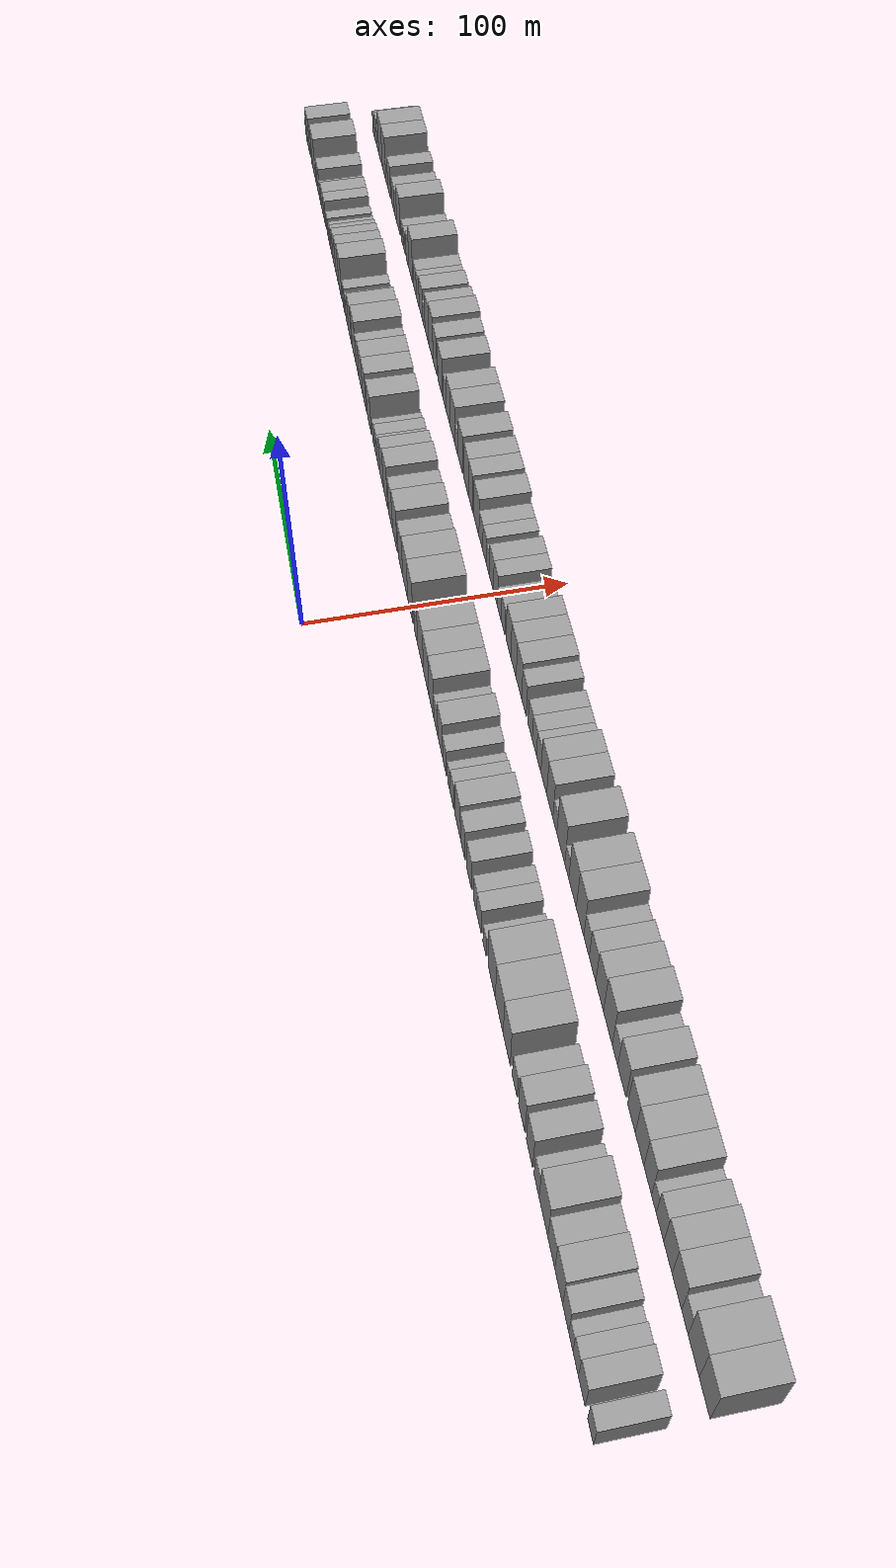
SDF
<sdf version="1.6">
 <world name="default">
  <scene>
   <sky><clouds><speed>12</speed></clouds></sky>
   <ambient>0.4 0.4 0.4 1</ambient>
   <background>0.7 0.7 0.7 1</background>
   <shadows>1</shadows>
  </scene>
  <gravity>0 0 -9.8066</gravity>
  <magnetic_field>6e-06 2.3e-05 -4.2e-05</magnetic_field>
  <physics default="0" name="default_physics" type="ode">
   <ode>
    <solver>
     <type>quick</type>
     <iters>10</iters>
     <sor>1.0</sor>
     <use_dynamic_moi_rescaling>0</use_dynamic_moi_rescaling>
    </solver>
    <constraints>
     <cfm>0</cfm>
     <erp>0.2</erp>
     <contact_max_correcting_vel>100</contact_max_correcting_vel>
     <contact_surface_layer>0.001</contact_surface_layer>
    </constraints>
   </ode>
   <max_step_size>0.004</max_step_size>
   <real_time_factor>1</real_time_factor>
   <real_time_update_rate>250</real_time_update_rate>
  </physics>
  <light name="sun" type="directional">
   <pose>0 0 10 0 0 0</pose>
   <diffuse>0.8 0.8 0.8 1</diffuse>
   <specular>0.2 0.2 0.2 1</specular>
   <attenuation>
    <range>1000</range>
    <constant>0.9</constant>
    <linear>0.01</linear>
    <quadratic>0.001</quadratic>
   </attenuation>
   <direction>-0.5 0.1 -0.9</direction>
  </light>
  <model name="building_1">
   <static>1</static>
   <pose>50.0000 -280.7641 0 0.000000 0.000000 0.000000</pose>
   <link name="link">
    <pose>0 0 7.50 0 0 0</pose>
    <collision name="collision"><geometry><box><size>20.0000 6.4718 15.0000</size></box></geometry></collision>
    <visual name="visual">
     <cast_shadows>0</cast_shadows>
     <geometry><box><size>20.0000 6.4718 15.0000</size></box></geometry>
     <material>
      <script>
       <uri>model://grey_wall/materials/scripts</uri>
       <uri>model://grey_wall/materials/textures</uri>
       <name>vrc/grey_wall</name>
      </script>
     </material>
    </visual>
   </link>
  </model>
  <model name="building_2">
   <static>1</static>
   <pose>50.0000 -270.7405 0 0.000000 0.000000 0.000000</pose>
   <link name="link">
    <pose>0 0 9.00 0 0 0</pose>
    <collision name="collision"><geometry><box><size>20.0000 7.5755 18.0000</size></box></geometry></collision>
    <visual name="visual">
     <cast_shadows>0</cast_shadows>
     <geometry><box><size>20.0000 7.5755 18.0000</size></box></geometry>
     <material>
      <script>
       <uri>model://grey_wall/materials/scripts</uri>
       <uri>model://grey_wall/materials/textures</uri>
       <name>vrc/grey_wall</name>
      </script>
     </material>
    </visual>
   </link>
  </model>
  <model name="building_3">
   <static>1</static>
   <pose>50.0000 -263.7563 0 0.000000 0.000000 0.000000</pose>
   <link name="link">
    <pose>0 0 7.50 0 0 0</pose>
    <collision name="collision"><geometry><box><size>20.0000 6.3929 15.0000</size></box></geometry></collision>
    <visual name="visual">
     <cast_shadows>0</cast_shadows>
     <geometry><box><size>20.0000 6.3929 15.0000</size></box></geometry>
     <material>
      <script>
       <uri>model://grey_wall/materials/scripts</uri>
       <uri>model://grey_wall/materials/textures</uri>
       <name>vrc/grey_wall</name>
      </script>
     </material>
    </visual>
   </link>
  </model>
  <model name="building_4">
   <static>1</static>
   <pose>50.0000 -258.0644 0 0.000000 0.000000 0.000000</pose>
   <link name="link">
    <pose>0 0 6.00 0 0 0</pose>
    <collision name="collision"><geometry><box><size>20.0000 4.9910 12.0000</size></box></geometry></collision>
    <visual name="visual">
     <cast_shadows>0</cast_shadows>
     <geometry><box><size>20.0000 4.9910 12.0000</size></box></geometry>
     <material>
      <script>
       <uri>model://grey_wall/materials/scripts</uri>
       <uri>model://grey_wall/materials/textures</uri>
       <name>vrc/grey_wall</name>
      </script>
     </material>
    </visual>
   </link>
  </model>
  <model name="building_5">
   <static>1</static>
   <pose>50.0000 -251.9622 0 0.000000 0.000000 0.000000</pose>
   <link name="link">
    <pose>0 0 9.00 0 0 0</pose>
    <collision name="collision"><geometry><box><size>20.0000 7.2133 18.0000</size></box></geometry></collision>
    <visual name="visual">
     <cast_shadows>0</cast_shadows>
     <geometry><box><size>20.0000 7.2133 18.0000</size></box></geometry>
     <material>
      <script>
       <uri>model://grey_wall/materials/scripts</uri>
       <uri>model://grey_wall/materials/textures</uri>
       <name>vrc/grey_wall</name>
      </script>
     </material>
    </visual>
   </link>
  </model>
  <model name="building_6">
   <static>1</static>
   <pose>50.0000 -243.4948 0 0.000000 0.000000 0.000000</pose>
   <link name="link">
    <pose>0 0 10.50 0 0 0</pose>
    <collision name="collision"><geometry><box><size>20.0000 9.7216 21.0000</size></box></geometry></collision>
    <visual name="visual">
     <cast_shadows>0</cast_shadows>
     <geometry><box><size>20.0000 9.7216 21.0000</size></box></geometry>
     <material>
      <script>
       <uri>model://grey_wall/materials/scripts</uri>
       <uri>model://grey_wall/materials/textures</uri>
       <name>vrc/grey_wall</name>
      </script>
     </material>
    </visual>
   </link>
  </model>
  <model name="building_7">
   <static>1</static>
   <pose>50.0000 -234.2494 0 0.000000 0.000000 0.000000</pose>
   <link name="link">
    <pose>0 0 9.00 0 0 0</pose>
    <collision name="collision"><geometry><box><size>20.0000 8.7690 18.0000</size></box></geometry></collision>
    <visual name="visual">
     <cast_shadows>0</cast_shadows>
     <geometry><box><size>20.0000 8.7690 18.0000</size></box></geometry>
     <material>
      <script>
       <uri>model://grey_wall/materials/scripts</uri>
       <uri>model://grey_wall/materials/textures</uri>
       <name>vrc/grey_wall</name>
      </script>
     </material>
    </visual>
   </link>
  </model>
  <model name="building_8">
   <static>1</static>
   <pose>50.0000 -224.1580 0 0.000000 0.000000 0.000000</pose>
   <link name="link">
    <pose>0 0 12.00 0 0 0</pose>
    <collision name="collision"><geometry><box><size>20.0000 11.4138 24.0000</size></box></geometry></collision>
    <visual name="visual">
     <cast_shadows>0</cast_shadows>
     <geometry><box><size>20.0000 11.4138 24.0000</size></box></geometry>
     <material>
      <script>
       <uri>model://grey_wall/materials/scripts</uri>
       <uri>model://grey_wall/materials/textures</uri>
       <name>vrc/grey_wall</name>
      </script>
     </material>
    </visual>
   </link>
  </model>
  <model name="building_9">
   <static>1</static>
   <pose>50.0000 -215.1167 0 0.000000 0.000000 0.000000</pose>
   <link name="link">
    <pose>0 0 7.50 0 0 0</pose>
    <collision name="collision"><geometry><box><size>20.0000 6.6688 15.0000</size></box></geometry></collision>
    <visual name="visual">
     <cast_shadows>0</cast_shadows>
     <geometry><box><size>20.0000 6.6688 15.0000</size></box></geometry>
     <material>
      <script>
       <uri>model://grey_wall/materials/scripts</uri>
       <uri>model://grey_wall/materials/textures</uri>
       <name>vrc/grey_wall</name>
      </script>
     </material>
    </visual>
   </link>
  </model>
  <model name="building_10">
   <static>1</static>
   <pose>50.0000 -205.5650 0 0.000000 0.000000 0.000000</pose>
   <link name="link">
    <pose>0 0 10.50 0 0 0</pose>
    <collision name="collision"><geometry><box><size>20.0000 8.4345 21.0000</size></box></geometry></collision>
    <visual name="visual">
     <cast_shadows>0</cast_shadows>
     <geometry><box><size>20.0000 8.4345 21.0000</size></box></geometry>
     <material>
      <script>
       <uri>model://grey_wall/materials/scripts</uri>
       <uri>model://grey_wall/materials/textures</uri>
       <name>vrc/grey_wall</name>
      </script>
     </material>
    </visual>
   </link>
  </model>
  <model name="building_11">
   <static>1</static>
   <pose>50.0000 -194.9145 0 0.000000 0.000000 0.000000</pose>
   <link name="link">
    <pose>0 0 10.50 0 0 0</pose>
    <collision name="collision"><geometry><box><size>20.0000 8.8665 21.0000</size></box></geometry></collision>
    <visual name="visual">
     <cast_shadows>0</cast_shadows>
     <geometry><box><size>20.0000 8.8665 21.0000</size></box></geometry>
     <material>
      <script>
       <uri>model://grey_wall/materials/scripts</uri>
       <uri>model://grey_wall/materials/textures</uri>
       <name>vrc/grey_wall</name>
      </script>
     </material>
    </visual>
   </link>
  </model>
  <model name="building_12">
   <static>1</static>
   <pose>50.0000 -185.0316 0 0.000000 0.000000 0.000000</pose>
   <link name="link">
    <pose>0 0 7.50 0 0 0</pose>
    <collision name="collision"><geometry><box><size>20.0000 6.8995 15.0000</size></box></geometry></collision>
    <visual name="visual">
     <cast_shadows>0</cast_shadows>
     <geometry><box><size>20.0000 6.8995 15.0000</size></box></geometry>
     <material>
      <script>
       <uri>model://grey_wall/materials/scripts</uri>
       <uri>model://grey_wall/materials/textures</uri>
       <name>vrc/grey_wall</name>
      </script>
     </material>
    </visual>
   </link>
  </model>
  <model name="building_13">
   <static>1</static>
   <pose>50.0000 -173.4004 0 0.000000 0.000000 0.000000</pose>
   <link name="link">
    <pose>0 0 12.00 0 0 0</pose>
    <collision name="collision"><geometry><box><size>20.0000 10.3628 24.0000</size></box></geometry></collision>
    <visual name="visual">
     <cast_shadows>0</cast_shadows>
     <geometry><box><size>20.0000 10.3628 24.0000</size></box></geometry>
     <material>
      <script>
       <uri>model://grey_wall/materials/scripts</uri>
       <uri>model://grey_wall/materials/textures</uri>
       <name>vrc/grey_wall</name>
      </script>
     </material>
    </visual>
   </link>
  </model>
  <model name="building_14">
   <static>1</static>
   <pose>50.0000 -162.3088 0 0.000000 0.000000 0.000000</pose>
   <link name="link">
    <pose>0 0 12.00 0 0 0</pose>
    <collision name="collision"><geometry><box><size>20.0000 11.8206 24.0000</size></box></geometry></collision>
    <visual name="visual">
     <cast_shadows>0</cast_shadows>
     <geometry><box><size>20.0000 11.8206 24.0000</size></box></geometry>
     <material>
      <script>
       <uri>model://grey_wall/materials/scripts</uri>
       <uri>model://grey_wall/materials/textures</uri>
       <name>vrc/grey_wall</name>
      </script>
     </material>
    </visual>
   </link>
  </model>
  <model name="building_15">
   <static>1</static>
   <pose>50.0000 -150.6447 0 0.000000 0.000000 0.000000</pose>
   <link name="link">
    <pose>0 0 12.00 0 0 0</pose>
    <collision name="collision"><geometry><box><size>20.0000 11.5075 24.0000</size></box></geometry></collision>
    <visual name="visual">
     <cast_shadows>0</cast_shadows>
     <geometry><box><size>20.0000 11.5075 24.0000</size></box></geometry>
     <material>
      <script>
       <uri>model://grey_wall/materials/scripts</uri>
       <uri>model://grey_wall/materials/textures</uri>
       <name>vrc/grey_wall</name>
      </script>
     </material>
    </visual>
   </link>
  </model>
  <model name="building_16">
   <static>1</static>
   <pose>50.0000 -139.3656 0 0.000000 0.000000 0.000000</pose>
   <link name="link">
    <pose>0 0 6.00 0 0 0</pose>
    <collision name="collision"><geometry><box><size>20.0000 5.0506 12.0000</size></box></geometry></collision>
    <visual name="visual">
     <cast_shadows>0</cast_shadows>
     <geometry><box><size>20.0000 5.0506 12.0000</size></box></geometry>
     <material>
      <script>
       <uri>model://grey_wall/materials/scripts</uri>
       <uri>model://grey_wall/materials/textures</uri>
       <name>vrc/grey_wall</name>
      </script>
     </material>
    </visual>
   </link>
  </model>
  <model name="building_17">
   <static>1</static>
   <pose>50.0000 -130.4451 0 0.000000 0.000000 0.000000</pose>
   <link name="link">
    <pose>0 0 7.50 0 0 0</pose>
    <collision name="collision"><geometry><box><size>20.0000 6.7904 15.0000</size></box></geometry></collision>
    <visual name="visual">
     <cast_shadows>0</cast_shadows>
     <geometry><box><size>20.0000 6.7904 15.0000</size></box></geometry>
     <material>
      <script>
       <uri>model://grey_wall/materials/scripts</uri>
       <uri>model://grey_wall/materials/textures</uri>
       <name>vrc/grey_wall</name>
      </script>
     </material>
    </visual>
   </link>
  </model>
  <model name="building_18">
   <static>1</static>
   <pose>50.0000 -123.9897 0 0.000000 0.000000 0.000000</pose>
   <link name="link">
    <pose>0 0 7.50 0 0 0</pose>
    <collision name="collision"><geometry><box><size>20.0000 6.1204 15.0000</size></box></geometry></collision>
    <visual name="visual">
     <cast_shadows>0</cast_shadows>
     <geometry><box><size>20.0000 6.1204 15.0000</size></box></geometry>
     <material>
      <script>
       <uri>model://grey_wall/materials/scripts</uri>
       <uri>model://grey_wall/materials/textures</uri>
       <name>vrc/grey_wall</name>
      </script>
     </material>
    </visual>
   </link>
  </model>
  <model name="building_19">
   <static>1</static>
   <pose>50.0000 -113.9621 0 0.000000 0.000000 0.000000</pose>
   <link name="link">
    <pose>0 0 9.00 0 0 0</pose>
    <collision name="collision"><geometry><box><size>20.0000 7.9350 18.0000</size></box></geometry></collision>
    <visual name="visual">
     <cast_shadows>0</cast_shadows>
     <geometry><box><size>20.0000 7.9350 18.0000</size></box></geometry>
     <material>
      <script>
       <uri>model://grey_wall/materials/scripts</uri>
       <uri>model://grey_wall/materials/textures</uri>
       <name>vrc/grey_wall</name>
      </script>
     </material>
    </visual>
   </link>
  </model>
  <model name="building_20">
   <static>1</static>
   <pose>50.0000 -102.9871 0 0.000000 0.000000 0.000000</pose>
   <link name="link">
    <pose>0 0 9.00 0 0 0</pose>
    <collision name="collision"><geometry><box><size>20.0000 8.0151 18.0000</size></box></geometry></collision>
    <visual name="visual">
     <cast_shadows>0</cast_shadows>
     <geometry><box><size>20.0000 8.0151 18.0000</size></box></geometry>
     <material>
      <script>
       <uri>model://grey_wall/materials/scripts</uri>
       <uri>model://grey_wall/materials/textures</uri>
       <name>vrc/grey_wall</name>
      </script>
     </material>
    </visual>
   </link>
  </model>
  <model name="building_21">
   <static>1</static>
   <pose>50.0000 -94.2392 0 0.000000 0.000000 0.000000</pose>
   <link name="link">
    <pose>0 0 10.50 0 0 0</pose>
    <collision name="collision"><geometry><box><size>20.0000 9.4808 21.0000</size></box></geometry></collision>
    <visual name="visual">
     <cast_shadows>0</cast_shadows>
     <geometry><box><size>20.0000 9.4808 21.0000</size></box></geometry>
     <material>
      <script>
       <uri>model://grey_wall/materials/scripts</uri>
       <uri>model://grey_wall/materials/textures</uri>
       <name>vrc/grey_wall</name>
      </script>
     </material>
    </visual>
   </link>
  </model>
  <model name="building_22">
   <static>1</static>
   <pose>50.0000 -84.2171 0 0.000000 0.000000 0.000000</pose>
   <link name="link">
    <pose>0 0 7.50 0 0 0</pose>
    <collision name="collision"><geometry><box><size>20.0000 6.5634 15.0000</size></box></geometry></collision>
    <visual name="visual">
     <cast_shadows>0</cast_shadows>
     <geometry><box><size>20.0000 6.5634 15.0000</size></box></geometry>
     <material>
      <script>
       <uri>model://grey_wall/materials/scripts</uri>
       <uri>model://grey_wall/materials/textures</uri>
       <name>vrc/grey_wall</name>
      </script>
     </material>
    </visual>
   </link>
  </model>
  <model name="building_23">
   <static>1</static>
   <pose>50.0000 -78.3758 0 0.000000 0.000000 0.000000</pose>
   <link name="link">
    <pose>0 0 6.00 0 0 0</pose>
    <collision name="collision"><geometry><box><size>20.0000 5.1192 12.0000</size></box></geometry></collision>
    <visual name="visual">
     <cast_shadows>0</cast_shadows>
     <geometry><box><size>20.0000 5.1192 12.0000</size></box></geometry>
     <material>
      <script>
       <uri>model://grey_wall/materials/scripts</uri>
       <uri>model://grey_wall/materials/textures</uri>
       <name>vrc/grey_wall</name>
      </script>
     </material>
    </visual>
   </link>
  </model>
  <model name="building_24">
   <static>1</static>
   <pose>50.0000 -70.3879 0 0.000000 0.000000 0.000000</pose>
   <link name="link">
    <pose>0 0 7.50 0 0 0</pose>
    <collision name="collision"><geometry><box><size>20.0000 6.8567 15.0000</size></box></geometry></collision>
    <visual name="visual">
     <cast_shadows>0</cast_shadows>
     <geometry><box><size>20.0000 6.8567 15.0000</size></box></geometry>
     <material>
      <script>
       <uri>model://grey_wall/materials/scripts</uri>
       <uri>model://grey_wall/materials/textures</uri>
       <name>vrc/grey_wall</name>
      </script>
     </material>
    </visual>
   </link>
  </model>
  <model name="building_25">
   <static>1</static>
   <pose>50.0000 -62.2291 0 0.000000 0.000000 0.000000</pose>
   <link name="link">
    <pose>0 0 10.50 0 0 0</pose>
    <collision name="collision"><geometry><box><size>20.0000 9.4610 21.0000</size></box></geometry></collision>
    <visual name="visual">
     <cast_shadows>0</cast_shadows>
     <geometry><box><size>20.0000 9.4610 21.0000</size></box></geometry>
     <material>
      <script>
       <uri>model://grey_wall/materials/scripts</uri>
       <uri>model://grey_wall/materials/textures</uri>
       <name>vrc/grey_wall</name>
      </script>
     </material>
    </visual>
   </link>
  </model>
  <model name="building_26">
   <static>1</static>
   <pose>50.0000 -53.7525 0 0.000000 0.000000 0.000000</pose>
   <link name="link">
    <pose>0 0 7.50 0 0 0</pose>
    <collision name="collision"><geometry><box><size>20.0000 7.4922 15.0000</size></box></geometry></collision>
    <visual name="visual">
     <cast_shadows>0</cast_shadows>
     <geometry><box><size>20.0000 7.4922 15.0000</size></box></geometry>
     <material>
      <script>
       <uri>model://grey_wall/materials/scripts</uri>
       <uri>model://grey_wall/materials/textures</uri>
       <name>vrc/grey_wall</name>
      </script>
     </material>
    </visual>
   </link>
  </model>
  <model name="building_27">
   <static>1</static>
   <pose>50.0000 -44.9499 0 0.000000 0.000000 0.000000</pose>
   <link name="link">
    <pose>0 0 12.00 0 0 0</pose>
    <collision name="collision"><geometry><box><size>20.0000 10.1128 24.0000</size></box></geometry></collision>
    <visual name="visual">
     <cast_shadows>0</cast_shadows>
     <geometry><box><size>20.0000 10.1128 24.0000</size></box></geometry>
     <material>
      <script>
       <uri>model://grey_wall/materials/scripts</uri>
       <uri>model://grey_wall/materials/textures</uri>
       <name>vrc/grey_wall</name>
      </script>
     </material>
    </visual>
   </link>
  </model>
  <model name="building_28">
   <static>1</static>
   <pose>50.0000 -34.6139 0 0.000000 0.000000 0.000000</pose>
   <link name="link">
    <pose>0 0 12.00 0 0 0</pose>
    <collision name="collision"><geometry><box><size>20.0000 10.5593 24.0000</size></box></geometry></collision>
    <visual name="visual">
     <cast_shadows>0</cast_shadows>
     <geometry><box><size>20.0000 10.5593 24.0000</size></box></geometry>
     <material>
      <script>
       <uri>model://grey_wall/materials/scripts</uri>
       <uri>model://grey_wall/materials/textures</uri>
       <name>vrc/grey_wall</name>
      </script>
     </material>
    </visual>
   </link>
  </model>
  <model name="building_29">
   <static>1</static>
   <pose>50.0000 -23.3891 0 0.000000 0.000000 0.000000</pose>
   <link name="link">
    <pose>0 0 12.00 0 0 0</pose>
    <collision name="collision"><geometry><box><size>20.0000 11.8902 24.0000</size></box></geometry></collision>
    <visual name="visual">
     <cast_shadows>0</cast_shadows>
     <geometry><box><size>20.0000 11.8902 24.0000</size></box></geometry>
     <material>
      <script>
       <uri>model://grey_wall/materials/scripts</uri>
       <uri>model://grey_wall/materials/textures</uri>
       <name>vrc/grey_wall</name>
      </script>
     </material>
    </visual>
   </link>
  </model>
  <model name="building_30">
   <static>1</static>
   <pose>50.0000 -14.0289 0 0.000000 0.000000 0.000000</pose>
   <link name="link">
    <pose>0 0 7.50 0 0 0</pose>
    <collision name="collision"><geometry><box><size>20.0000 6.8303 15.0000</size></box></geometry></collision>
    <visual name="visual">
     <cast_shadows>0</cast_shadows>
     <geometry><box><size>20.0000 6.8303 15.0000</size></box></geometry>
     <material>
      <script>
       <uri>model://grey_wall/materials/scripts</uri>
       <uri>model://grey_wall/materials/textures</uri>
       <name>vrc/grey_wall</name>
      </script>
     </material>
    </visual>
   </link>
  </model>
  <model name="building_31">
   <static>1</static>
   <pose>50.0000 -1.9353 0 0.000000 0.000000 0.000000</pose>
   <link name="link">
    <pose>0 0 12.00 0 0 0</pose>
    <collision name="collision"><geometry><box><size>20.0000 11.3569 24.0000</size></box></geometry></collision>
    <visual name="visual">
     <cast_shadows>0</cast_shadows>
     <geometry><box><size>20.0000 11.3569 24.0000</size></box></geometry>
     <material>
      <script>
       <uri>model://grey_wall/materials/scripts</uri>
       <uri>model://grey_wall/materials/textures</uri>
       <name>vrc/grey_wall</name>
      </script>
     </material>
    </visual>
   </link>
  </model>
  <model name="building_32">
   <static>1</static>
   <pose>50.0000 9.2240 0 0.000000 0.000000 0.000000</pose>
   <link name="link">
    <pose>0 0 12.00 0 0 0</pose>
    <collision name="collision"><geometry><box><size>20.0000 10.9616 24.0000</size></box></geometry></collision>
    <visual name="visual">
     <cast_shadows>0</cast_shadows>
     <geometry><box><size>20.0000 10.9616 24.0000</size></box></geometry>
     <material>
      <script>
       <uri>model://grey_wall/materials/scripts</uri>
       <uri>model://grey_wall/materials/textures</uri>
       <name>vrc/grey_wall</name>
      </script>
     </material>
    </visual>
   </link>
  </model>
  <model name="building_33">
   <static>1</static>
   <pose>50.0000 19.7706 0 0.000000 0.000000 0.000000</pose>
   <link name="link">
    <pose>0 0 10.50 0 0 0</pose>
    <collision name="collision"><geometry><box><size>20.0000 10.1318 21.0000</size></box></geometry></collision>
    <visual name="visual">
     <cast_shadows>0</cast_shadows>
     <geometry><box><size>20.0000 10.1318 21.0000</size></box></geometry>
     <material>
      <script>
       <uri>model://grey_wall/materials/scripts</uri>
       <uri>model://grey_wall/materials/textures</uri>
       <name>vrc/grey_wall</name>
      </script>
     </material>
    </visual>
   </link>
  </model>
  <model name="building_34">
   <static>1</static>
   <pose>50.0000 32.3000 0 0.000000 0.000000 0.000000</pose>
   <link name="link">
    <pose>0 0 12.00 0 0 0</pose>
    <collision name="collision"><geometry><box><size>20.0000 10.9269 24.0000</size></box></geometry></collision>
    <visual name="visual">
     <cast_shadows>0</cast_shadows>
     <geometry><box><size>20.0000 10.9269 24.0000</size></box></geometry>
     <material>
      <script>
       <uri>model://grey_wall/materials/scripts</uri>
       <uri>model://grey_wall/materials/textures</uri>
       <name>vrc/grey_wall</name>
      </script>
     </material>
    </visual>
   </link>
  </model>
  <model name="building_35">
   <static>1</static>
   <pose>50.0000 42.4426 0 0.000000 0.000000 0.000000</pose>
   <link name="link">
    <pose>0 0 10.50 0 0 0</pose>
    <collision name="collision"><geometry><box><size>20.0000 9.3583 21.0000</size></box></geometry></collision>
    <visual name="visual">
     <cast_shadows>0</cast_shadows>
     <geometry><box><size>20.0000 9.3583 21.0000</size></box></geometry>
     <material>
      <script>
       <uri>model://grey_wall/materials/scripts</uri>
       <uri>model://grey_wall/materials/textures</uri>
       <name>vrc/grey_wall</name>
      </script>
     </material>
    </visual>
   </link>
  </model>
  <model name="building_36">
   <static>1</static>
   <pose>50.0000 54.1233 0 0.000000 0.000000 0.000000</pose>
   <link name="link">
    <pose>0 0 12.00 0 0 0</pose>
    <collision name="collision"><geometry><box><size>20.0000 10.0030 24.0000</size></box></geometry></collision>
    <visual name="visual">
     <cast_shadows>0</cast_shadows>
     <geometry><box><size>20.0000 10.0030 24.0000</size></box></geometry>
     <material>
      <script>
       <uri>model://grey_wall/materials/scripts</uri>
       <uri>model://grey_wall/materials/textures</uri>
       <name>vrc/grey_wall</name>
      </script>
     </material>
    </visual>
   </link>
  </model>
  <model name="building_37">
   <static>1</static>
   <pose>50.0000 63.5357 0 0.000000 0.000000 0.000000</pose>
   <link name="link">
    <pose>0 0 10.50 0 0 0</pose>
    <collision name="collision"><geometry><box><size>20.0000 8.8218 21.0000</size></box></geometry></collision>
    <visual name="visual">
     <cast_shadows>0</cast_shadows>
     <geometry><box><size>20.0000 8.8218 21.0000</size></box></geometry>
     <material>
      <script>
       <uri>model://grey_wall/materials/scripts</uri>
       <uri>model://grey_wall/materials/textures</uri>
       <name>vrc/grey_wall</name>
      </script>
     </material>
    </visual>
   </link>
  </model>
  <model name="building_38">
   <static>1</static>
   <pose>50.0000 71.4498 0 0.000000 0.000000 0.000000</pose>
   <link name="link">
    <pose>0 0 7.50 0 0 0</pose>
    <collision name="collision"><geometry><box><size>20.0000 7.0064 15.0000</size></box></geometry></collision>
    <visual name="visual">
     <cast_shadows>0</cast_shadows>
     <geometry><box><size>20.0000 7.0064 15.0000</size></box></geometry>
     <material>
      <script>
       <uri>model://grey_wall/materials/scripts</uri>
       <uri>model://grey_wall/materials/textures</uri>
       <name>vrc/grey_wall</name>
      </script>
     </material>
    </visual>
   </link>
  </model>
  <model name="building_39">
   <static>1</static>
   <pose>50.0000 77.9659 0 0.000000 0.000000 0.000000</pose>
   <link name="link">
    <pose>0 0 7.50 0 0 0</pose>
    <collision name="collision"><geometry><box><size>20.0000 6.0259 15.0000</size></box></geometry></collision>
    <visual name="visual">
     <cast_shadows>0</cast_shadows>
     <geometry><box><size>20.0000 6.0259 15.0000</size></box></geometry>
     <material>
      <script>
       <uri>model://grey_wall/materials/scripts</uri>
       <uri>model://grey_wall/materials/textures</uri>
       <name>vrc/grey_wall</name>
      </script>
     </material>
    </visual>
   </link>
  </model>
  <model name="building_40">
   <static>1</static>
   <pose>50.0000 83.8761 0 0.000000 0.000000 0.000000</pose>
   <link name="link">
    <pose>0 0 6.00 0 0 0</pose>
    <collision name="collision"><geometry><box><size>20.0000 5.7946 12.0000</size></box></geometry></collision>
    <visual name="visual">
     <cast_shadows>0</cast_shadows>
     <geometry><box><size>20.0000 5.7946 12.0000</size></box></geometry>
     <material>
      <script>
       <uri>model://grey_wall/materials/scripts</uri>
       <uri>model://grey_wall/materials/textures</uri>
       <name>vrc/grey_wall</name>
      </script>
     </material>
    </visual>
   </link>
  </model>
  <model name="building_41">
   <static>1</static>
   <pose>50.0000 94.9250 0 0.000000 0.000000 0.000000</pose>
   <link name="link">
    <pose>0 0 10.50 0 0 0</pose>
    <collision name="collision"><geometry><box><size>20.0000 10.3031 21.0000</size></box></geometry></collision>
    <visual name="visual">
     <cast_shadows>0</cast_shadows>
     <geometry><box><size>20.0000 10.3031 21.0000</size></box></geometry>
     <material>
      <script>
       <uri>model://grey_wall/materials/scripts</uri>
       <uri>model://grey_wall/materials/textures</uri>
       <name>vrc/grey_wall</name>
      </script>
     </material>
    </visual>
   </link>
  </model>
  <model name="building_42">
   <static>1</static>
   <pose>50.0000 107.9998 0 0.000000 0.000000 0.000000</pose>
   <link name="link">
    <pose>0 0 10.50 0 0 0</pose>
    <collision name="collision"><geometry><box><size>20.0000 9.8465 21.0000</size></box></geometry></collision>
    <visual name="visual">
     <cast_shadows>0</cast_shadows>
     <geometry><box><size>20.0000 9.8465 21.0000</size></box></geometry>
     <material>
      <script>
       <uri>model://grey_wall/materials/scripts</uri>
       <uri>model://grey_wall/materials/textures</uri>
       <name>vrc/grey_wall</name>
      </script>
     </material>
    </visual>
   </link>
  </model>
  <model name="building_43">
   <static>1</static>
   <pose>50.0000 117.6652 0 0.000000 0.000000 0.000000</pose>
   <link name="link">
    <pose>0 0 10.50 0 0 0</pose>
    <collision name="collision"><geometry><box><size>20.0000 9.4843 21.0000</size></box></geometry></collision>
    <visual name="visual">
     <cast_shadows>0</cast_shadows>
     <geometry><box><size>20.0000 9.4843 21.0000</size></box></geometry>
     <material>
      <script>
       <uri>model://grey_wall/materials/scripts</uri>
       <uri>model://grey_wall/materials/textures</uri>
       <name>vrc/grey_wall</name>
      </script>
     </material>
    </visual>
   </link>
  </model>
  <model name="building_44">
   <static>1</static>
   <pose>50.0000 126.3931 0 0.000000 0.000000 0.000000</pose>
   <link name="link">
    <pose>0 0 9.00 0 0 0</pose>
    <collision name="collision"><geometry><box><size>20.0000 7.9715 18.0000</size></box></geometry></collision>
    <visual name="visual">
     <cast_shadows>0</cast_shadows>
     <geometry><box><size>20.0000 7.9715 18.0000</size></box></geometry>
     <material>
      <script>
       <uri>model://grey_wall/materials/scripts</uri>
       <uri>model://grey_wall/materials/textures</uri>
       <name>vrc/grey_wall</name>
      </script>
     </material>
    </visual>
   </link>
  </model>
  <model name="building_45">
   <static>1</static>
   <pose>50.0000 135.6400 0 0.000000 0.000000 0.000000</pose>
   <link name="link">
    <pose>0 0 12.00 0 0 0</pose>
    <collision name="collision"><geometry><box><size>20.0000 10.5224 24.0000</size></box></geometry></collision>
    <visual name="visual">
     <cast_shadows>0</cast_shadows>
     <geometry><box><size>20.0000 10.5224 24.0000</size></box></geometry>
     <material>
      <script>
       <uri>model://grey_wall/materials/scripts</uri>
       <uri>model://grey_wall/materials/textures</uri>
       <name>vrc/grey_wall</name>
      </script>
     </material>
    </visual>
   </link>
  </model>
  <model name="building_46">
   <static>1</static>
   <pose>50.0000 147.3809 0 0.000000 0.000000 0.000000</pose>
   <link name="link">
    <pose>0 0 10.50 0 0 0</pose>
    <collision name="collision"><geometry><box><size>20.0000 8.9595 21.0000</size></box></geometry></collision>
    <visual name="visual">
     <cast_shadows>0</cast_shadows>
     <geometry><box><size>20.0000 8.9595 21.0000</size></box></geometry>
     <material>
      <script>
       <uri>model://grey_wall/materials/scripts</uri>
       <uri>model://grey_wall/materials/textures</uri>
       <name>vrc/grey_wall</name>
      </script>
     </material>
    </visual>
   </link>
  </model>
  <model name="building_47">
   <static>1</static>
   <pose>50.0000 155.5785 0 0.000000 0.000000 0.000000</pose>
   <link name="link">
    <pose>0 0 7.50 0 0 0</pose>
    <collision name="collision"><geometry><box><size>20.0000 7.4357 15.0000</size></box></geometry></collision>
    <visual name="visual">
     <cast_shadows>0</cast_shadows>
     <geometry><box><size>20.0000 7.4357 15.0000</size></box></geometry>
     <material>
      <script>
       <uri>model://grey_wall/materials/scripts</uri>
       <uri>model://grey_wall/materials/textures</uri>
       <name>vrc/grey_wall</name>
      </script>
     </material>
    </visual>
   </link>
  </model>
  <model name="building_48">
   <static>1</static>
   <pose>50.0000 164.2977 0 0.000000 0.000000 0.000000</pose>
   <link name="link">
    <pose>0 0 7.50 0 0 0</pose>
    <collision name="collision"><geometry><box><size>20.0000 6.0026 15.0000</size></box></geometry></collision>
    <visual name="visual">
     <cast_shadows>0</cast_shadows>
     <geometry><box><size>20.0000 6.0026 15.0000</size></box></geometry>
     <material>
      <script>
       <uri>model://grey_wall/materials/scripts</uri>
       <uri>model://grey_wall/materials/textures</uri>
       <name>vrc/grey_wall</name>
      </script>
     </material>
    </visual>
   </link>
  </model>
  <model name="building_49">
   <static>1</static>
   <pose>50.0000 175.1931 0 0.000000 0.000000 0.000000</pose>
   <link name="link">
    <pose>0 0 12.00 0 0 0</pose>
    <collision name="collision"><geometry><box><size>20.0000 9.7882 24.0000</size></box></geometry></collision>
    <visual name="visual">
     <cast_shadows>0</cast_shadows>
     <geometry><box><size>20.0000 9.7882 24.0000</size></box></geometry>
     <material>
      <script>
       <uri>model://grey_wall/materials/scripts</uri>
       <uri>model://grey_wall/materials/textures</uri>
       <name>vrc/grey_wall</name>
      </script>
     </material>
    </visual>
   </link>
  </model>
  <model name="building_50">
   <static>1</static>
   <pose>50.0000 184.7946 0 0.000000 0.000000 0.000000</pose>
   <link name="link">
    <pose>0 0 10.50 0 0 0</pose>
    <collision name="collision"><geometry><box><size>20.0000 9.4149 21.0000</size></box></geometry></collision>
    <visual name="visual">
     <cast_shadows>0</cast_shadows>
     <geometry><box><size>20.0000 9.4149 21.0000</size></box></geometry>
     <material>
      <script>
       <uri>model://grey_wall/materials/scripts</uri>
       <uri>model://grey_wall/materials/textures</uri>
       <name>vrc/grey_wall</name>
      </script>
     </material>
    </visual>
   </link>
  </model>
  <model name="building_51">
   <static>1</static>
   <pose>50.0000 193.7850 0 0.000000 0.000000 0.000000</pose>
   <link name="link">
    <pose>0 0 9.00 0 0 0</pose>
    <collision name="collision"><geometry><box><size>20.0000 8.5659 18.0000</size></box></geometry></collision>
    <visual name="visual">
     <cast_shadows>0</cast_shadows>
     <geometry><box><size>20.0000 8.5659 18.0000</size></box></geometry>
     <material>
      <script>
       <uri>model://grey_wall/materials/scripts</uri>
       <uri>model://grey_wall/materials/textures</uri>
       <name>vrc/grey_wall</name>
      </script>
     </material>
    </visual>
   </link>
  </model>
  <model name="building_52">
   <static>1</static>
   <pose>50.0000 201.1514 0 0.000000 0.000000 0.000000</pose>
   <link name="link">
    <pose>0 0 7.50 0 0 0</pose>
    <collision name="collision"><geometry><box><size>20.0000 6.1670 15.0000</size></box></geometry></collision>
    <visual name="visual">
     <cast_shadows>0</cast_shadows>
     <geometry><box><size>20.0000 6.1670 15.0000</size></box></geometry>
     <material>
      <script>
       <uri>model://grey_wall/materials/scripts</uri>
       <uri>model://grey_wall/materials/textures</uri>
       <name>vrc/grey_wall</name>
      </script>
     </material>
    </visual>
   </link>
  </model>
  <model name="building_53">
   <static>1</static>
   <pose>50.0000 207.1415 0 0.000000 0.000000 0.000000</pose>
   <link name="link">
    <pose>0 0 6.00 0 0 0</pose>
    <collision name="collision"><geometry><box><size>20.0000 5.8132 12.0000</size></box></geometry></collision>
    <visual name="visual">
     <cast_shadows>0</cast_shadows>
     <geometry><box><size>20.0000 5.8132 12.0000</size></box></geometry>
     <material>
      <script>
       <uri>model://grey_wall/materials/scripts</uri>
       <uri>model://grey_wall/materials/textures</uri>
       <name>vrc/grey_wall</name>
      </script>
     </material>
    </visual>
   </link>
  </model>
  <model name="building_54">
   <static>1</static>
   <pose>50.0000 214.7163 0 0.000000 0.000000 0.000000</pose>
   <link name="link">
    <pose>0 0 6.00 0 0 0</pose>
    <collision name="collision"><geometry><box><size>20.0000 5.3364 12.0000</size></box></geometry></collision>
    <visual name="visual">
     <cast_shadows>0</cast_shadows>
     <geometry><box><size>20.0000 5.3364 12.0000</size></box></geometry>
     <material>
      <script>
       <uri>model://grey_wall/materials/scripts</uri>
       <uri>model://grey_wall/materials/textures</uri>
       <name>vrc/grey_wall</name>
      </script>
     </material>
    </visual>
   </link>
  </model>
  <model name="building_55">
   <static>1</static>
   <pose>50.0000 223.6519 0 0.000000 0.000000 0.000000</pose>
   <link name="link">
    <pose>0 0 7.50 0 0 0</pose>
    <collision name="collision"><geometry><box><size>20.0000 6.5347 15.0000</size></box></geometry></collision>
    <visual name="visual">
     <cast_shadows>0</cast_shadows>
     <geometry><box><size>20.0000 6.5347 15.0000</size></box></geometry>
     <material>
      <script>
       <uri>model://grey_wall/materials/scripts</uri>
       <uri>model://grey_wall/materials/textures</uri>
       <name>vrc/grey_wall</name>
      </script>
     </material>
    </visual>
   </link>
  </model>
  <model name="building_56">
   <static>1</static>
   <pose>50.0000 230.6128 0 0.000000 0.000000 0.000000</pose>
   <link name="link">
    <pose>0 0 7.50 0 0 0</pose>
    <collision name="collision"><geometry><box><size>20.0000 7.3871 15.0000</size></box></geometry></collision>
    <visual name="visual">
     <cast_shadows>0</cast_shadows>
     <geometry><box><size>20.0000 7.3871 15.0000</size></box></geometry>
     <material>
      <script>
       <uri>model://grey_wall/materials/scripts</uri>
       <uri>model://grey_wall/materials/textures</uri>
       <name>vrc/grey_wall</name>
      </script>
     </material>
    </visual>
   </link>
  </model>
  <model name="building_57">
   <static>1</static>
   <pose>50.0000 236.8439 0 0.000000 0.000000 0.000000</pose>
   <link name="link">
    <pose>0 0 6.00 0 0 0</pose>
    <collision name="collision"><geometry><box><size>20.0000 5.0752 12.0000</size></box></geometry></collision>
    <visual name="visual">
     <cast_shadows>0</cast_shadows>
     <geometry><box><size>20.0000 5.0752 12.0000</size></box></geometry>
     <material>
      <script>
       <uri>model://grey_wall/materials/scripts</uri>
       <uri>model://grey_wall/materials/textures</uri>
       <name>vrc/grey_wall</name>
      </script>
     </material>
    </visual>
   </link>
  </model>
  <model name="building_58">
   <static>1</static>
   <pose>50.0000 243.7710 0 0.000000 0.000000 0.000000</pose>
   <link name="link">
    <pose>0 0 9.00 0 0 0</pose>
    <collision name="collision"><geometry><box><size>20.0000 8.7789 18.0000</size></box></geometry></collision>
    <visual name="visual">
     <cast_shadows>0</cast_shadows>
     <geometry><box><size>20.0000 8.7789 18.0000</size></box></geometry>
     <material>
      <script>
       <uri>model://grey_wall/materials/scripts</uri>
       <uri>model://grey_wall/materials/textures</uri>
       <name>vrc/grey_wall</name>
      </script>
     </material>
    </visual>
   </link>
  </model>
  <model name="building_59">
   <static>1</static>
   <pose>50.0000 250.7922 0 0.000000 0.000000 0.000000</pose>
   <link name="link">
    <pose>0 0 6.00 0 0 0</pose>
    <collision name="collision"><geometry><box><size>20.0000 5.2635 12.0000</size></box></geometry></collision>
    <visual name="visual">
     <cast_shadows>0</cast_shadows>
     <geometry><box><size>20.0000 5.2635 12.0000</size></box></geometry>
     <material>
      <script>
       <uri>model://grey_wall/materials/scripts</uri>
       <uri>model://grey_wall/materials/textures</uri>
       <name>vrc/grey_wall</name>
      </script>
     </material>
    </visual>
   </link>
  </model>
  <model name="building_60">
   <static>1</static>
   <pose>50.0000 259.3824 0 0.000000 0.000000 0.000000</pose>
   <link name="link">
    <pose>0 0 12.00 0 0 0</pose>
    <collision name="collision"><geometry><box><size>20.0000 11.9169 24.0000</size></box></geometry></collision>
    <visual name="visual">
     <cast_shadows>0</cast_shadows>
     <geometry><box><size>20.0000 11.9169 24.0000</size></box></geometry>
     <material>
      <script>
       <uri>model://grey_wall/materials/scripts</uri>
       <uri>model://grey_wall/materials/textures</uri>
       <name>vrc/grey_wall</name>
      </script>
     </material>
    </visual>
   </link>
  </model>
  <model name="building_61">
   <static>1</static>
   <pose>50.0000 267.8239 0 0.000000 0.000000 0.000000</pose>
   <link name="link">
    <pose>0 0 6.00 0 0 0</pose>
    <collision name="collision"><geometry><box><size>20.0000 4.9660 12.0000</size></box></geometry></collision>
    <visual name="visual">
     <cast_shadows>0</cast_shadows>
     <geometry><box><size>20.0000 4.9660 12.0000</size></box></geometry>
     <material>
      <script>
       <uri>model://grey_wall/materials/scripts</uri>
       <uri>model://grey_wall/materials/textures</uri>
       <name>vrc/grey_wall</name>
      </script>
     </material>
    </visual>
   </link>
  </model>
  <model name="building_62">
   <static>1</static>
   <pose>50.0000 278.0380 0 0.000000 0.000000 0.000000</pose>
   <link name="link">
    <pose>0 0 10.50 0 0 0</pose>
    <collision name="collision"><geometry><box><size>20.0000 9.4623 21.0000</size></box></geometry></collision>
    <visual name="visual">
     <cast_shadows>0</cast_shadows>
     <geometry><box><size>20.0000 9.4623 21.0000</size></box></geometry>
     <material>
      <script>
       <uri>model://grey_wall/materials/scripts</uri>
       <uri>model://grey_wall/materials/textures</uri>
       <name>vrc/grey_wall</name>
      </script>
     </material>
    </visual>
   </link>
  </model>
  <model name="building_63">
   <static>1</static>
   <pose>50.0000 285.2360 0 0.000000 0.000000 0.000000</pose>
   <link name="link">
    <pose>0 0 6.00 0 0 0</pose>
    <collision name="collision"><geometry><box><size>20.0000 4.9337 12.0000</size></box></geometry></collision>
    <visual name="visual">
     <cast_shadows>0</cast_shadows>
     <geometry><box><size>20.0000 4.9337 12.0000</size></box></geometry>
     <material>
      <script>
       <uri>model://grey_wall/materials/scripts</uri>
       <uri>model://grey_wall/materials/textures</uri>
       <name>vrc/grey_wall</name>
      </script>
     </material>
    </visual>
   </link>
  </model>
  <model name="building_64">
   <static>1</static>
   <pose>82.0000 -278.7919 0 0.000000 0.000000 0.000000</pose>
   <link name="link">
    <pose>0 0 12.00 0 0 0</pose>
    <collision name="collision"><geometry><box><size>20.0000 10.4161 24.0000</size></box></geometry></collision>
    <visual name="visual">
     <cast_shadows>0</cast_shadows>
     <geometry><box><size>20.0000 10.4161 24.0000</size></box></geometry>
     <material>
      <script>
       <uri>model://grey_wall/materials/scripts</uri>
       <uri>model://grey_wall/materials/textures</uri>
       <name>vrc/grey_wall</name>
      </script>
     </material>
    </visual>
   </link>
  </model>
  <model name="building_65">
   <static>1</static>
   <pose>82.0000 -268.0944 0 0.000000 0.000000 0.000000</pose>
   <link name="link">
    <pose>0 0 12.00 0 0 0</pose>
    <collision name="collision"><geometry><box><size>20.0000 10.9790 24.0000</size></box></geometry></collision>
    <visual name="visual">
     <cast_shadows>0</cast_shadows>
     <geometry><box><size>20.0000 10.9790 24.0000</size></box></geometry>
     <material>
      <script>
       <uri>model://grey_wall/materials/scripts</uri>
       <uri>model://grey_wall/materials/textures</uri>
       <name>vrc/grey_wall</name>
      </script>
     </material>
    </visual>
   </link>
  </model>
  <model name="building_66">
   <static>1</static>
   <pose>82.0000 -259.3315 0 0.000000 0.000000 0.000000</pose>
   <link name="link">
    <pose>0 0 7.50 0 0 0</pose>
    <collision name="collision"><geometry><box><size>20.0000 6.5467 15.0000</size></box></geometry></collision>
    <visual name="visual">
     <cast_shadows>0</cast_shadows>
     <geometry><box><size>20.0000 6.5467 15.0000</size></box></geometry>
     <material>
      <script>
       <uri>model://grey_wall/materials/scripts</uri>
       <uri>model://grey_wall/materials/textures</uri>
       <name>vrc/grey_wall</name>
      </script>
     </material>
    </visual>
   </link>
  </model>
  <model name="building_67">
   <static>1</static>
   <pose>82.0000 -251.1312 0 0.000000 0.000000 0.000000</pose>
   <link name="link">
    <pose>0 0 10.50 0 0 0</pose>
    <collision name="collision"><geometry><box><size>20.0000 9.8540 21.0000</size></box></geometry></collision>
    <visual name="visual">
     <cast_shadows>0</cast_shadows>
     <geometry><box><size>20.0000 9.8540 21.0000</size></box></geometry>
     <material>
      <script>
       <uri>model://grey_wall/materials/scripts</uri>
       <uri>model://grey_wall/materials/textures</uri>
       <name>vrc/grey_wall</name>
      </script>
     </material>
    </visual>
   </link>
  </model>
  <model name="building_68">
   <static>1</static>
   <pose>82.0000 -241.8199 0 0.000000 0.000000 0.000000</pose>
   <link name="link">
    <pose>0 0 10.50 0 0 0</pose>
    <collision name="collision"><geometry><box><size>20.0000 8.7685 21.0000</size></box></geometry></collision>
    <visual name="visual">
     <cast_shadows>0</cast_shadows>
     <geometry><box><size>20.0000 8.7685 21.0000</size></box></geometry>
     <material>
      <script>
       <uri>model://grey_wall/materials/scripts</uri>
       <uri>model://grey_wall/materials/textures</uri>
       <name>vrc/grey_wall</name>
      </script>
     </material>
    </visual>
   </link>
  </model>
  <model name="building_69">
   <static>1</static>
   <pose>82.0000 -233.3877 0 0.000000 0.000000 0.000000</pose>
   <link name="link">
    <pose>0 0 9.00 0 0 0</pose>
    <collision name="collision"><geometry><box><size>20.0000 8.0960 18.0000</size></box></geometry></collision>
    <visual name="visual">
     <cast_shadows>0</cast_shadows>
     <geometry><box><size>20.0000 8.0960 18.0000</size></box></geometry>
     <material>
      <script>
       <uri>model://grey_wall/materials/scripts</uri>
       <uri>model://grey_wall/materials/textures</uri>
       <name>vrc/grey_wall</name>
      </script>
     </material>
    </visual>
   </link>
  </model>
  <model name="building_70">
   <static>1</static>
   <pose>82.0000 -226.7633 0 0.000000 0.000000 0.000000</pose>
   <link name="link">
    <pose>0 0 6.00 0 0 0</pose>
    <collision name="collision"><geometry><box><size>20.0000 5.1528 12.0000</size></box></geometry></collision>
    <visual name="visual">
     <cast_shadows>0</cast_shadows>
     <geometry><box><size>20.0000 5.1528 12.0000</size></box></geometry>
     <material>
      <script>
       <uri>model://grey_wall/materials/scripts</uri>
       <uri>model://grey_wall/materials/textures</uri>
       <name>vrc/grey_wall</name>
      </script>
     </material>
    </visual>
   </link>
  </model>
  <model name="building_71">
   <static>1</static>
   <pose>82.0000 -219.9043 0 0.000000 0.000000 0.000000</pose>
   <link name="link">
    <pose>0 0 10.50 0 0 0</pose>
    <collision name="collision"><geometry><box><size>20.0000 8.5651 21.0000</size></box></geometry></collision>
    <visual name="visual">
     <cast_shadows>0</cast_shadows>
     <geometry><box><size>20.0000 8.5651 21.0000</size></box></geometry>
     <material>
      <script>
       <uri>model://grey_wall/materials/scripts</uri>
       <uri>model://grey_wall/materials/textures</uri>
       <name>vrc/grey_wall</name>
      </script>
     </material>
    </visual>
   </link>
  </model>
  <model name="building_72">
   <static>1</static>
   <pose>82.0000 -210.6769 0 0.000000 0.000000 0.000000</pose>
   <link name="link">
    <pose>0 0 10.50 0 0 0</pose>
    <collision name="collision"><geometry><box><size>20.0000 9.8898 21.0000</size></box></geometry></collision>
    <visual name="visual">
     <cast_shadows>0</cast_shadows>
     <geometry><box><size>20.0000 9.8898 21.0000</size></box></geometry>
     <material>
      <script>
       <uri>model://grey_wall/materials/scripts</uri>
       <uri>model://grey_wall/materials/textures</uri>
       <name>vrc/grey_wall</name>
      </script>
     </material>
    </visual>
   </link>
  </model>
  <model name="building_73">
   <static>1</static>
   <pose>82.0000 -201.2730 0 0.000000 0.000000 0.000000</pose>
   <link name="link">
    <pose>0 0 10.50 0 0 0</pose>
    <collision name="collision"><geometry><box><size>20.0000 8.9179 21.0000</size></box></geometry></collision>
    <visual name="visual">
     <cast_shadows>0</cast_shadows>
     <geometry><box><size>20.0000 8.9179 21.0000</size></box></geometry>
     <material>
      <script>
       <uri>model://grey_wall/materials/scripts</uri>
       <uri>model://grey_wall/materials/textures</uri>
       <name>vrc/grey_wall</name>
      </script>
     </material>
    </visual>
   </link>
  </model>
  <model name="building_74">
   <static>1</static>
   <pose>82.0000 -189.8234 0 0.000000 0.000000 0.000000</pose>
   <link name="link">
    <pose>0 0 10.50 0 0 0</pose>
    <collision name="collision"><geometry><box><size>20.0000 9.9813 21.0000</size></box></geometry></collision>
    <visual name="visual">
     <cast_shadows>0</cast_shadows>
     <geometry><box><size>20.0000 9.9813 21.0000</size></box></geometry>
     <material>
      <script>
       <uri>model://grey_wall/materials/scripts</uri>
       <uri>model://grey_wall/materials/textures</uri>
       <name>vrc/grey_wall</name>
      </script>
     </material>
    </visual>
   </link>
  </model>
  <model name="building_75">
   <static>1</static>
   <pose>82.0000 -181.4269 0 0.000000 0.000000 0.000000</pose>
   <link name="link">
    <pose>0 0 7.50 0 0 0</pose>
    <collision name="collision"><geometry><box><size>20.0000 6.8117 15.0000</size></box></geometry></collision>
    <visual name="visual">
     <cast_shadows>0</cast_shadows>
     <geometry><box><size>20.0000 6.8117 15.0000</size></box></geometry>
     <material>
      <script>
       <uri>model://grey_wall/materials/scripts</uri>
       <uri>model://grey_wall/materials/textures</uri>
       <name>vrc/grey_wall</name>
      </script>
     </material>
    </visual>
   </link>
  </model>
  <model name="building_76">
   <static>1</static>
   <pose>82.0000 -172.5177 0 0.000000 0.000000 0.000000</pose>
   <link name="link">
    <pose>0 0 12.00 0 0 0</pose>
    <collision name="collision"><geometry><box><size>20.0000 11.0067 24.0000</size></box></geometry></collision>
    <visual name="visual">
     <cast_shadows>0</cast_shadows>
     <geometry><box><size>20.0000 11.0067 24.0000</size></box></geometry>
     <material>
      <script>
       <uri>model://grey_wall/materials/scripts</uri>
       <uri>model://grey_wall/materials/textures</uri>
       <name>vrc/grey_wall</name>
      </script>
     </material>
    </visual>
   </link>
  </model>
  <model name="building_77">
   <static>1</static>
   <pose>82.0000 -162.0368 0 0.000000 0.000000 0.000000</pose>
   <link name="link">
    <pose>0 0 10.50 0 0 0</pose>
    <collision name="collision"><geometry><box><size>20.0000 9.9552 21.0000</size></box></geometry></collision>
    <visual name="visual">
     <cast_shadows>0</cast_shadows>
     <geometry><box><size>20.0000 9.9552 21.0000</size></box></geometry>
     <material>
      <script>
       <uri>model://grey_wall/materials/scripts</uri>
       <uri>model://grey_wall/materials/textures</uri>
       <name>vrc/grey_wall</name>
      </script>
     </material>
    </visual>
   </link>
  </model>
  <model name="building_78">
   <static>1</static>
   <pose>82.0000 -152.7214 0 0.000000 0.000000 0.000000</pose>
   <link name="link">
    <pose>0 0 9.00 0 0 0</pose>
    <collision name="collision"><geometry><box><size>20.0000 8.6756 18.0000</size></box></geometry></collision>
    <visual name="visual">
     <cast_shadows>0</cast_shadows>
     <geometry><box><size>20.0000 8.6756 18.0000</size></box></geometry>
     <material>
      <script>
       <uri>model://grey_wall/materials/scripts</uri>
       <uri>model://grey_wall/materials/textures</uri>
       <name>vrc/grey_wall</name>
      </script>
     </material>
    </visual>
   </link>
  </model>
  <model name="building_79">
   <static>1</static>
   <pose>82.0000 -144.7593 0 0.000000 0.000000 0.000000</pose>
   <link name="link">
    <pose>0 0 7.50 0 0 0</pose>
    <collision name="collision"><geometry><box><size>20.0000 7.2486 15.0000</size></box></geometry></collision>
    <visual name="visual">
     <cast_shadows>0</cast_shadows>
     <geometry><box><size>20.0000 7.2486 15.0000</size></box></geometry>
     <material>
      <script>
       <uri>model://grey_wall/materials/scripts</uri>
       <uri>model://grey_wall/materials/textures</uri>
       <name>vrc/grey_wall</name>
      </script>
     </material>
    </visual>
   </link>
  </model>
  <model name="building_80">
   <static>1</static>
   <pose>82.0000 -136.0414 0 0.000000 0.000000 0.000000</pose>
   <link name="link">
    <pose>0 0 12.00 0 0 0</pose>
    <collision name="collision"><geometry><box><size>20.0000 10.1873 24.0000</size></box></geometry></collision>
    <visual name="visual">
     <cast_shadows>0</cast_shadows>
     <geometry><box><size>20.0000 10.1873 24.0000</size></box></geometry>
     <material>
      <script>
       <uri>model://grey_wall/materials/scripts</uri>
       <uri>model://grey_wall/materials/textures</uri>
       <name>vrc/grey_wall</name>
      </script>
     </material>
    </visual>
   </link>
  </model>
  <model name="building_81">
   <static>1</static>
   <pose>82.0000 -125.6295 0 0.000000 0.000000 0.000000</pose>
   <link name="link">
    <pose>0 0 12.00 0 0 0</pose>
    <collision name="collision"><geometry><box><size>20.0000 10.6364 24.0000</size></box></geometry></collision>
    <visual name="visual">
     <cast_shadows>0</cast_shadows>
     <geometry><box><size>20.0000 10.6364 24.0000</size></box></geometry>
     <material>
      <script>
       <uri>model://grey_wall/materials/scripts</uri>
       <uri>model://grey_wall/materials/textures</uri>
       <name>vrc/grey_wall</name>
      </script>
     </material>
    </visual>
   </link>
  </model>
  <model name="building_82">
   <static>1</static>
   <pose>82.0000 -117.4550 0 0.000000 0.000000 0.000000</pose>
   <link name="link">
    <pose>0 0 6.00 0 0 0</pose>
    <collision name="collision"><geometry><box><size>20.0000 5.7126 12.0000</size></box></geometry></collision>
    <visual name="visual">
     <cast_shadows>0</cast_shadows>
     <geometry><box><size>20.0000 5.7126 12.0000</size></box></geometry>
     <material>
      <script>
       <uri>model://grey_wall/materials/scripts</uri>
       <uri>model://grey_wall/materials/textures</uri>
       <name>vrc/grey_wall</name>
      </script>
     </material>
    </visual>
   </link>
  </model>
  <model name="building_83">
   <static>1</static>
   <pose>82.0000 -108.7943 0 0.000000 0.000000 0.000000</pose>
   <link name="link">
    <pose>0 0 12.00 0 0 0</pose>
    <collision name="collision"><geometry><box><size>20.0000 11.6089 24.0000</size></box></geometry></collision>
    <visual name="visual">
     <cast_shadows>0</cast_shadows>
     <geometry><box><size>20.0000 11.6089 24.0000</size></box></geometry>
     <material>
      <script>
       <uri>model://grey_wall/materials/scripts</uri>
       <uri>model://grey_wall/materials/textures</uri>
       <name>vrc/grey_wall</name>
      </script>
     </material>
    </visual>
   </link>
  </model>
  <model name="building_84">
   <static>1</static>
   <pose>82.0000 -100.0545 0 0.000000 0.000000 0.000000</pose>
   <link name="link">
    <pose>0 0 6.00 0 0 0</pose>
    <collision name="collision"><geometry><box><size>20.0000 5.8708 12.0000</size></box></geometry></collision>
    <visual name="visual">
     <cast_shadows>0</cast_shadows>
     <geometry><box><size>20.0000 5.8708 12.0000</size></box></geometry>
     <material>
      <script>
       <uri>model://grey_wall/materials/scripts</uri>
       <uri>model://grey_wall/materials/textures</uri>
       <name>vrc/grey_wall</name>
      </script>
     </material>
    </visual>
   </link>
  </model>
  <model name="building_85">
   <static>1</static>
   <pose>82.0000 -92.4165 0 0.000000 0.000000 0.000000</pose>
   <link name="link">
    <pose>0 0 10.50 0 0 0</pose>
    <collision name="collision"><geometry><box><size>20.0000 9.4053 21.0000</size></box></geometry></collision>
    <visual name="visual">
     <cast_shadows>0</cast_shadows>
     <geometry><box><size>20.0000 9.4053 21.0000</size></box></geometry>
     <material>
      <script>
       <uri>model://grey_wall/materials/scripts</uri>
       <uri>model://grey_wall/materials/textures</uri>
       <name>vrc/grey_wall</name>
      </script>
     </material>
    </visual>
   </link>
  </model>
  <model name="building_86">
   <static>1</static>
   <pose>82.0000 -83.2509 0 0.000000 0.000000 0.000000</pose>
   <link name="link">
    <pose>0 0 10.50 0 0 0</pose>
    <collision name="collision"><geometry><box><size>20.0000 8.9259 21.0000</size></box></geometry></collision>
    <visual name="visual">
     <cast_shadows>0</cast_shadows>
     <geometry><box><size>20.0000 8.9259 21.0000</size></box></geometry>
     <material>
      <script>
       <uri>model://grey_wall/materials/scripts</uri>
       <uri>model://grey_wall/materials/textures</uri>
       <name>vrc/grey_wall</name>
      </script>
     </material>
    </visual>
   </link>
  </model>
  <model name="building_87">
   <static>1</static>
   <pose>82.0000 -75.2861 0 0.000000 0.000000 0.000000</pose>
   <link name="link">
    <pose>0 0 7.50 0 0 0</pose>
    <collision name="collision"><geometry><box><size>20.0000 7.0036 15.0000</size></box></geometry></collision>
    <visual name="visual">
     <cast_shadows>0</cast_shadows>
     <geometry><box><size>20.0000 7.0036 15.0000</size></box></geometry>
     <material>
      <script>
       <uri>model://grey_wall/materials/scripts</uri>
       <uri>model://grey_wall/materials/textures</uri>
       <name>vrc/grey_wall</name>
      </script>
     </material>
    </visual>
   </link>
  </model>
  <model name="building_88">
   <static>1</static>
   <pose>82.0000 -68.4446 0 0.000000 0.000000 0.000000</pose>
   <link name="link">
    <pose>0 0 7.50 0 0 0</pose>
    <collision name="collision"><geometry><box><size>20.0000 6.6795 15.0000</size></box></geometry></collision>
    <visual name="visual">
     <cast_shadows>0</cast_shadows>
     <geometry><box><size>20.0000 6.6795 15.0000</size></box></geometry>
     <material>
      <script>
       <uri>model://grey_wall/materials/scripts</uri>
       <uri>model://grey_wall/materials/textures</uri>
       <name>vrc/grey_wall</name>
      </script>
     </material>
    </visual>
   </link>
  </model>
  <model name="building_89">
   <static>1</static>
   <pose>82.0000 -61.6841 0 0.000000 0.000000 0.000000</pose>
   <link name="link">
    <pose>0 0 7.50 0 0 0</pose>
    <collision name="collision"><geometry><box><size>20.0000 6.8414 15.0000</size></box></geometry></collision>
    <visual name="visual">
     <cast_shadows>0</cast_shadows>
     <geometry><box><size>20.0000 6.8414 15.0000</size></box></geometry>
     <material>
      <script>
       <uri>model://grey_wall/materials/scripts</uri>
       <uri>model://grey_wall/materials/textures</uri>
       <name>vrc/grey_wall</name>
      </script>
     </material>
    </visual>
   </link>
  </model>
  <model name="building_90">
   <static>1</static>
   <pose>82.0000 -51.4665 0 0.000000 0.000000 0.000000</pose>
   <link name="link">
    <pose>0 0 9.00 0 0 0</pose>
    <collision name="collision"><geometry><box><size>20.0000 7.5939 18.0000</size></box></geometry></collision>
    <visual name="visual">
     <cast_shadows>0</cast_shadows>
     <geometry><box><size>20.0000 7.5939 18.0000</size></box></geometry>
     <material>
      <script>
       <uri>model://grey_wall/materials/scripts</uri>
       <uri>model://grey_wall/materials/textures</uri>
       <name>vrc/grey_wall</name>
      </script>
     </material>
    </visual>
   </link>
  </model>
  <model name="building_91">
   <static>1</static>
   <pose>82.0000 -43.0854 0 0.000000 0.000000 0.000000</pose>
   <link name="link">
    <pose>0 0 10.50 0 0 0</pose>
    <collision name="collision"><geometry><box><size>20.0000 9.1684 21.0000</size></box></geometry></collision>
    <visual name="visual">
     <cast_shadows>0</cast_shadows>
     <geometry><box><size>20.0000 9.1684 21.0000</size></box></geometry>
     <material>
      <script>
       <uri>model://grey_wall/materials/scripts</uri>
       <uri>model://grey_wall/materials/textures</uri>
       <name>vrc/grey_wall</name>
      </script>
     </material>
    </visual>
   </link>
  </model>
  <model name="building_92">
   <static>1</static>
   <pose>82.0000 -33.9232 0 0.000000 0.000000 0.000000</pose>
   <link name="link">
    <pose>0 0 10.50 0 0 0</pose>
    <collision name="collision"><geometry><box><size>20.0000 9.1559 21.0000</size></box></geometry></collision>
    <visual name="visual">
     <cast_shadows>0</cast_shadows>
     <geometry><box><size>20.0000 9.1559 21.0000</size></box></geometry>
     <material>
      <script>
       <uri>model://grey_wall/materials/scripts</uri>
       <uri>model://grey_wall/materials/textures</uri>
       <name>vrc/grey_wall</name>
      </script>
     </material>
    </visual>
   </link>
  </model>
  <model name="building_93">
   <static>1</static>
   <pose>82.0000 -25.1346 0 0.000000 0.000000 0.000000</pose>
   <link name="link">
    <pose>0 0 10.50 0 0 0</pose>
    <collision name="collision"><geometry><box><size>20.0000 8.4212 21.0000</size></box></geometry></collision>
    <visual name="visual">
     <cast_shadows>0</cast_shadows>
     <geometry><box><size>20.0000 8.4212 21.0000</size></box></geometry>
     <material>
      <script>
       <uri>model://grey_wall/materials/scripts</uri>
       <uri>model://grey_wall/materials/textures</uri>
       <name>vrc/grey_wall</name>
      </script>
     </material>
    </visual>
   </link>
  </model>
  <model name="building_94">
   <static>1</static>
   <pose>82.0000 -15.3508 0 0.000000 0.000000 0.000000</pose>
   <link name="link">
    <pose>0 0 7.50 0 0 0</pose>
    <collision name="collision"><geometry><box><size>20.0000 7.1466 15.0000</size></box></geometry></collision>
    <visual name="visual">
     <cast_shadows>0</cast_shadows>
     <geometry><box><size>20.0000 7.1466 15.0000</size></box></geometry>
     <material>
      <script>
       <uri>model://grey_wall/materials/scripts</uri>
       <uri>model://grey_wall/materials/textures</uri>
       <name>vrc/grey_wall</name>
      </script>
     </material>
    </visual>
   </link>
  </model>
  <model name="building_95">
   <static>1</static>
   <pose>82.0000 -8.8649 0 0.000000 0.000000 0.000000</pose>
   <link name="link">
    <pose>0 0 6.00 0 0 0</pose>
    <collision name="collision"><geometry><box><size>20.0000 5.8251 12.0000</size></box></geometry></collision>
    <visual name="visual">
     <cast_shadows>0</cast_shadows>
     <geometry><box><size>20.0000 5.8251 12.0000</size></box></geometry>
     <material>
      <script>
       <uri>model://grey_wall/materials/scripts</uri>
       <uri>model://grey_wall/materials/textures</uri>
       <name>vrc/grey_wall</name>
      </script>
     </material>
    </visual>
   </link>
  </model>
  <model name="building_96">
   <static>1</static>
   <pose>82.0000 -2.1464 0 0.000000 0.000000 0.000000</pose>
   <link name="link">
    <pose>0 0 9.00 0 0 0</pose>
    <collision name="collision"><geometry><box><size>20.0000 7.6120 18.0000</size></box></geometry></collision>
    <visual name="visual">
     <cast_shadows>0</cast_shadows>
     <geometry><box><size>20.0000 7.6120 18.0000</size></box></geometry>
     <material>
      <script>
       <uri>model://grey_wall/materials/scripts</uri>
       <uri>model://grey_wall/materials/textures</uri>
       <name>vrc/grey_wall</name>
      </script>
     </material>
    </visual>
   </link>
  </model>
  <model name="building_97">
   <static>1</static>
   <pose>82.0000 5.7058 0 0.000000 0.000000 0.000000</pose>
   <link name="link">
    <pose>0 0 9.00 0 0 0</pose>
    <collision name="collision"><geometry><box><size>20.0000 8.0926 18.0000</size></box></geometry></collision>
    <visual name="visual">
     <cast_shadows>0</cast_shadows>
     <geometry><box><size>20.0000 8.0926 18.0000</size></box></geometry>
     <material>
      <script>
       <uri>model://grey_wall/materials/scripts</uri>
       <uri>model://grey_wall/materials/textures</uri>
       <name>vrc/grey_wall</name>
      </script>
     </material>
    </visual>
   </link>
  </model>
  <model name="building_98">
   <static>1</static>
   <pose>82.0000 12.2922 0 0.000000 0.000000 0.000000</pose>
   <link name="link">
    <pose>0 0 6.00 0 0 0</pose>
    <collision name="collision"><geometry><box><size>20.0000 5.0802 12.0000</size></box></geometry></collision>
    <visual name="visual">
     <cast_shadows>0</cast_shadows>
     <geometry><box><size>20.0000 5.0802 12.0000</size></box></geometry>
     <material>
      <script>
       <uri>model://grey_wall/materials/scripts</uri>
       <uri>model://grey_wall/materials/textures</uri>
       <name>vrc/grey_wall</name>
      </script>
     </material>
    </visual>
   </link>
  </model>
  <model name="building_99">
   <static>1</static>
   <pose>82.0000 18.2237 0 0.000000 0.000000 0.000000</pose>
   <link name="link">
    <pose>0 0 7.50 0 0 0</pose>
    <collision name="collision"><geometry><box><size>20.0000 6.7827 15.0000</size></box></geometry></collision>
    <visual name="visual">
     <cast_shadows>0</cast_shadows>
     <geometry><box><size>20.0000 6.7827 15.0000</size></box></geometry>
     <material>
      <script>
       <uri>model://grey_wall/materials/scripts</uri>
       <uri>model://grey_wall/materials/textures</uri>
       <name>vrc/grey_wall</name>
      </script>
     </material>
    </visual>
   </link>
  </model>
  <model name="building_100">
   <static>1</static>
   <pose>82.0000 25.3104 0 0.000000 0.000000 0.000000</pose>
   <link name="link">
    <pose>0 0 7.50 0 0 0</pose>
    <collision name="collision"><geometry><box><size>20.0000 7.3907 15.0000</size></box></geometry></collision>
    <visual name="visual">
     <cast_shadows>0</cast_shadows>
     <geometry><box><size>20.0000 7.3907 15.0000</size></box></geometry>
     <material>
      <script>
       <uri>model://grey_wall/materials/scripts</uri>
       <uri>model://grey_wall/materials/textures</uri>
       <name>vrc/grey_wall</name>
      </script>
     </material>
    </visual>
   </link>
  </model>
  <model name="building_101">
   <static>1</static>
   <pose>82.0000 34.0197 0 0.000000 0.000000 0.000000</pose>
   <link name="link">
    <pose>0 0 10.50 0 0 0</pose>
    <collision name="collision"><geometry><box><size>20.0000 10.0278 21.0000</size></box></geometry></collision>
    <visual name="visual">
     <cast_shadows>0</cast_shadows>
     <geometry><box><size>20.0000 10.0278 21.0000</size></box></geometry>
     <material>
      <script>
       <uri>model://grey_wall/materials/scripts</uri>
       <uri>model://grey_wall/materials/textures</uri>
       <name>vrc/grey_wall</name>
      </script>
     </material>
    </visual>
   </link>
  </model>
  <model name="building_102">
   <static>1</static>
   <pose>82.0000 45.4800 0 0.000000 0.000000 0.000000</pose>
   <link name="link">
    <pose>0 0 10.50 0 0 0</pose>
    <collision name="collision"><geometry><box><size>20.0000 8.8928 21.0000</size></box></geometry></collision>
    <visual name="visual">
     <cast_shadows>0</cast_shadows>
     <geometry><box><size>20.0000 8.8928 21.0000</size></box></geometry>
     <material>
      <script>
       <uri>model://grey_wall/materials/scripts</uri>
       <uri>model://grey_wall/materials/textures</uri>
       <name>vrc/grey_wall</name>
      </script>
     </material>
    </visual>
   </link>
  </model>
  <model name="building_103">
   <static>1</static>
   <pose>82.0000 54.3152 0 0.000000 0.000000 0.000000</pose>
   <link name="link">
    <pose>0 0 10.50 0 0 0</pose>
    <collision name="collision"><geometry><box><size>20.0000 8.7777 21.0000</size></box></geometry></collision>
    <visual name="visual">
     <cast_shadows>0</cast_shadows>
     <geometry><box><size>20.0000 8.7777 21.0000</size></box></geometry>
     <material>
      <script>
       <uri>model://grey_wall/materials/scripts</uri>
       <uri>model://grey_wall/materials/textures</uri>
       <name>vrc/grey_wall</name>
      </script>
     </material>
    </visual>
   </link>
  </model>
  <model name="building_104">
   <static>1</static>
   <pose>82.0000 66.9151 0 0.000000 0.000000 0.000000</pose>
   <link name="link">
    <pose>0 0 10.50 0 0 0</pose>
    <collision name="collision"><geometry><box><size>20.0000 10.4221 21.0000</size></box></geometry></collision>
    <visual name="visual">
     <cast_shadows>0</cast_shadows>
     <geometry><box><size>20.0000 10.4221 21.0000</size></box></geometry>
     <material>
      <script>
       <uri>model://grey_wall/materials/scripts</uri>
       <uri>model://grey_wall/materials/textures</uri>
       <name>vrc/grey_wall</name>
      </script>
     </material>
    </visual>
   </link>
  </model>
  <model name="building_105">
   <static>1</static>
   <pose>82.0000 74.8989 0 0.000000 0.000000 0.000000</pose>
   <link name="link">
    <pose>0 0 6.00 0 0 0</pose>
    <collision name="collision"><geometry><box><size>20.0000 5.5454 12.0000</size></box></geometry></collision>
    <visual name="visual">
     <cast_shadows>0</cast_shadows>
     <geometry><box><size>20.0000 5.5454 12.0000</size></box></geometry>
     <material>
      <script>
       <uri>model://grey_wall/materials/scripts</uri>
       <uri>model://grey_wall/materials/textures</uri>
       <name>vrc/grey_wall</name>
      </script>
     </material>
    </visual>
   </link>
  </model>
  <model name="building_106">
   <static>1</static>
   <pose>82.0000 82.7951 0 0.000000 0.000000 0.000000</pose>
   <link name="link">
    <pose>0 0 10.50 0 0 0</pose>
    <collision name="collision"><geometry><box><size>20.0000 10.2469 21.0000</size></box></geometry></collision>
    <visual name="visual">
     <cast_shadows>0</cast_shadows>
     <geometry><box><size>20.0000 10.2469 21.0000</size></box></geometry>
     <material>
      <script>
       <uri>model://grey_wall/materials/scripts</uri>
       <uri>model://grey_wall/materials/textures</uri>
       <name>vrc/grey_wall</name>
      </script>
     </material>
    </visual>
   </link>
  </model>
  <model name="building_107">
   <static>1</static>
   <pose>82.0000 92.5687 0 0.000000 0.000000 0.000000</pose>
   <link name="link">
    <pose>0 0 10.50 0 0 0</pose>
    <collision name="collision"><geometry><box><size>20.0000 9.3003 21.0000</size></box></geometry></collision>
    <visual name="visual">
     <cast_shadows>0</cast_shadows>
     <geometry><box><size>20.0000 9.3003 21.0000</size></box></geometry>
     <material>
      <script>
       <uri>model://grey_wall/materials/scripts</uri>
       <uri>model://grey_wall/materials/textures</uri>
       <name>vrc/grey_wall</name>
      </script>
     </material>
    </visual>
   </link>
  </model>
  <model name="building_108">
   <static>1</static>
   <pose>82.0000 100.3097 0 0.000000 0.000000 0.000000</pose>
   <link name="link">
    <pose>0 0 7.50 0 0 0</pose>
    <collision name="collision"><geometry><box><size>20.0000 6.1818 15.0000</size></box></geometry></collision>
    <visual name="visual">
     <cast_shadows>0</cast_shadows>
     <geometry><box><size>20.0000 6.1818 15.0000</size></box></geometry>
     <material>
      <script>
       <uri>model://grey_wall/materials/scripts</uri>
       <uri>model://grey_wall/materials/textures</uri>
       <name>vrc/grey_wall</name>
      </script>
     </material>
    </visual>
   </link>
  </model>
  <model name="building_109">
   <static>1</static>
   <pose>82.0000 110.6427 0 0.000000 0.000000 0.000000</pose>
   <link name="link">
    <pose>0 0 10.50 0 0 0</pose>
    <collision name="collision"><geometry><box><size>20.0000 10.4842 21.0000</size></box></geometry></collision>
    <visual name="visual">
     <cast_shadows>0</cast_shadows>
     <geometry><box><size>20.0000 10.4842 21.0000</size></box></geometry>
     <material>
      <script>
       <uri>model://grey_wall/materials/scripts</uri>
       <uri>model://grey_wall/materials/textures</uri>
       <name>vrc/grey_wall</name>
      </script>
     </material>
    </visual>
   </link>
  </model>
  <model name="building_110">
   <static>1</static>
   <pose>82.0000 122.3761 0 0.000000 0.000000 0.000000</pose>
   <link name="link">
    <pose>0 0 10.50 0 0 0</pose>
    <collision name="collision"><geometry><box><size>20.0000 8.9828 21.0000</size></box></geometry></collision>
    <visual name="visual">
     <cast_shadows>0</cast_shadows>
     <geometry><box><size>20.0000 8.9828 21.0000</size></box></geometry>
     <material>
      <script>
       <uri>model://grey_wall/materials/scripts</uri>
       <uri>model://grey_wall/materials/textures</uri>
       <name>vrc/grey_wall</name>
      </script>
     </material>
    </visual>
   </link>
  </model>
  <model name="building_111">
   <static>1</static>
   <pose>82.0000 131.9106 0 0.000000 0.000000 0.000000</pose>
   <link name="link">
    <pose>0 0 12.00 0 0 0</pose>
    <collision name="collision"><geometry><box><size>20.0000 10.0862 24.0000</size></box></geometry></collision>
    <visual name="visual">
     <cast_shadows>0</cast_shadows>
     <geometry><box><size>20.0000 10.0862 24.0000</size></box></geometry>
     <material>
      <script>
       <uri>model://grey_wall/materials/scripts</uri>
       <uri>model://grey_wall/materials/textures</uri>
       <name>vrc/grey_wall</name>
      </script>
     </material>
    </visual>
   </link>
  </model>
  <model name="building_112">
   <static>1</static>
   <pose>82.0000 141.5262 0 0.000000 0.000000 0.000000</pose>
   <link name="link">
    <pose>0 0 10.50 0 0 0</pose>
    <collision name="collision"><geometry><box><size>20.0000 9.1451 21.0000</size></box></geometry></collision>
    <visual name="visual">
     <cast_shadows>0</cast_shadows>
     <geometry><box><size>20.0000 9.1451 21.0000</size></box></geometry>
     <material>
      <script>
       <uri>model://grey_wall/materials/scripts</uri>
       <uri>model://grey_wall/materials/textures</uri>
       <name>vrc/grey_wall</name>
      </script>
     </material>
    </visual>
   </link>
  </model>
  <model name="building_113">
   <static>1</static>
   <pose>82.0000 148.7313 0 0.000000 0.000000 0.000000</pose>
   <link name="link">
    <pose>0 0 6.00 0 0 0</pose>
    <collision name="collision"><geometry><box><size>20.0000 5.2650 12.0000</size></box></geometry></collision>
    <visual name="visual">
     <cast_shadows>0</cast_shadows>
     <geometry><box><size>20.0000 5.2650 12.0000</size></box></geometry>
     <material>
      <script>
       <uri>model://grey_wall/materials/scripts</uri>
       <uri>model://grey_wall/materials/textures</uri>
       <name>vrc/grey_wall</name>
      </script>
     </material>
    </visual>
   </link>
  </model>
  <model name="building_114">
   <static>1</static>
   <pose>82.0000 155.7561 0 0.000000 0.000000 0.000000</pose>
   <link name="link">
    <pose>0 0 9.00 0 0 0</pose>
    <collision name="collision"><geometry><box><size>20.0000 8.7845 18.0000</size></box></geometry></collision>
    <visual name="visual">
     <cast_shadows>0</cast_shadows>
     <geometry><box><size>20.0000 8.7845 18.0000</size></box></geometry>
     <material>
      <script>
       <uri>model://grey_wall/materials/scripts</uri>
       <uri>model://grey_wall/materials/textures</uri>
       <name>vrc/grey_wall</name>
      </script>
     </material>
    </visual>
   </link>
  </model>
  <model name="building_115">
   <static>1</static>
   <pose>82.0000 163.6476 0 0.000000 0.000000 0.000000</pose>
   <link name="link">
    <pose>0 0 7.50 0 0 0</pose>
    <collision name="collision"><geometry><box><size>20.0000 6.9985 15.0000</size></box></geometry></collision>
    <visual name="visual">
     <cast_shadows>0</cast_shadows>
     <geometry><box><size>20.0000 6.9985 15.0000</size></box></geometry>
     <material>
      <script>
       <uri>model://grey_wall/materials/scripts</uri>
       <uri>model://grey_wall/materials/textures</uri>
       <name>vrc/grey_wall</name>
      </script>
     </material>
    </visual>
   </link>
  </model>
  <model name="building_116">
   <static>1</static>
   <pose>82.0000 170.7134 0 0.000000 0.000000 0.000000</pose>
   <link name="link">
    <pose>0 0 7.50 0 0 0</pose>
    <collision name="collision"><geometry><box><size>20.0000 7.1330 15.0000</size></box></geometry></collision>
    <visual name="visual">
     <cast_shadows>0</cast_shadows>
     <geometry><box><size>20.0000 7.1330 15.0000</size></box></geometry>
     <material>
      <script>
       <uri>model://grey_wall/materials/scripts</uri>
       <uri>model://grey_wall/materials/textures</uri>
       <name>vrc/grey_wall</name>
      </script>
     </material>
    </visual>
   </link>
  </model>
  <model name="building_117">
   <static>1</static>
   <pose>82.0000 181.2088 0 0.000000 0.000000 0.000000</pose>
   <link name="link">
    <pose>0 0 12.00 0 0 0</pose>
    <collision name="collision"><geometry><box><size>20.0000 9.8578 24.0000</size></box></geometry></collision>
    <visual name="visual">
     <cast_shadows>0</cast_shadows>
     <geometry><box><size>20.0000 9.8578 24.0000</size></box></geometry>
     <material>
      <script>
       <uri>model://grey_wall/materials/scripts</uri>
       <uri>model://grey_wall/materials/textures</uri>
       <name>vrc/grey_wall</name>
      </script>
     </material>
    </visual>
   </link>
  </model>
  <model name="building_118">
   <static>1</static>
   <pose>82.0000 189.8162 0 0.000000 0.000000 0.000000</pose>
   <link name="link">
    <pose>0 0 7.50 0 0 0</pose>
    <collision name="collision"><geometry><box><size>20.0000 7.3570 15.0000</size></box></geometry></collision>
    <visual name="visual">
     <cast_shadows>0</cast_shadows>
     <geometry><box><size>20.0000 7.3570 15.0000</size></box></geometry>
     <material>
      <script>
       <uri>model://grey_wall/materials/scripts</uri>
       <uri>model://grey_wall/materials/textures</uri>
       <name>vrc/grey_wall</name>
      </script>
     </material>
    </visual>
   </link>
  </model>
  <model name="building_119">
   <static>1</static>
   <pose>82.0000 198.0587 0 0.000000 0.000000 0.000000</pose>
   <link name="link">
    <pose>0 0 6.00 0 0 0</pose>
    <collision name="collision"><geometry><box><size>20.0000 5.1281 12.0000</size></box></geometry></collision>
    <visual name="visual">
     <cast_shadows>0</cast_shadows>
     <geometry><box><size>20.0000 5.1281 12.0000</size></box></geometry>
     <material>
      <script>
       <uri>model://grey_wall/materials/scripts</uri>
       <uri>model://grey_wall/materials/textures</uri>
       <name>vrc/grey_wall</name>
      </script>
     </material>
    </visual>
   </link>
  </model>
  <model name="building_120">
   <static>1</static>
   <pose>82.0000 203.1987 0 0.000000 0.000000 0.000000</pose>
   <link name="link">
    <pose>0 0 6.00 0 0 0</pose>
    <collision name="collision"><geometry><box><size>20.0000 5.1518 12.0000</size></box></geometry></collision>
    <visual name="visual">
     <cast_shadows>0</cast_shadows>
     <geometry><box><size>20.0000 5.1518 12.0000</size></box></geometry>
     <material>
      <script>
       <uri>model://grey_wall/materials/scripts</uri>
       <uri>model://grey_wall/materials/textures</uri>
       <name>vrc/grey_wall</name>
      </script>
     </material>
    </visual>
   </link>
  </model>
  <model name="building_121">
   <static>1</static>
   <pose>82.0000 213.5785 0 0.000000 0.000000 0.000000</pose>
   <link name="link">
    <pose>0 0 10.50 0 0 0</pose>
    <collision name="collision"><geometry><box><size>20.0000 9.6078 21.0000</size></box></geometry></collision>
    <visual name="visual">
     <cast_shadows>0</cast_shadows>
     <geometry><box><size>20.0000 9.6078 21.0000</size></box></geometry>
     <material>
      <script>
       <uri>model://grey_wall/materials/scripts</uri>
       <uri>model://grey_wall/materials/textures</uri>
       <name>vrc/grey_wall</name>
      </script>
     </material>
    </visual>
   </link>
  </model>
  <model name="building_122">
   <static>1</static>
   <pose>82.0000 221.6331 0 0.000000 0.000000 0.000000</pose>
   <link name="link">
    <pose>0 0 7.50 0 0 0</pose>
    <collision name="collision"><geometry><box><size>20.0000 6.5015 15.0000</size></box></geometry></collision>
    <visual name="visual">
     <cast_shadows>0</cast_shadows>
     <geometry><box><size>20.0000 6.5015 15.0000</size></box></geometry>
     <material>
      <script>
       <uri>model://grey_wall/materials/scripts</uri>
       <uri>model://grey_wall/materials/textures</uri>
       <name>vrc/grey_wall</name>
      </script>
     </material>
    </visual>
   </link>
  </model>
  <model name="building_123">
   <static>1</static>
   <pose>82.0000 228.4155 0 0.000000 0.000000 0.000000</pose>
   <link name="link">
    <pose>0 0 7.50 0 0 0</pose>
    <collision name="collision"><geometry><box><size>20.0000 7.0634 15.0000</size></box></geometry></collision>
    <visual name="visual">
     <cast_shadows>0</cast_shadows>
     <geometry><box><size>20.0000 7.0634 15.0000</size></box></geometry>
     <material>
      <script>
       <uri>model://grey_wall/materials/scripts</uri>
       <uri>model://grey_wall/materials/textures</uri>
       <name>vrc/grey_wall</name>
      </script>
     </material>
    </visual>
   </link>
  </model>
  <model name="building_124">
   <static>1</static>
   <pose>82.0000 238.9627 0 0.000000 0.000000 0.000000</pose>
   <link name="link">
    <pose>0 0 9.00 0 0 0</pose>
    <collision name="collision"><geometry><box><size>20.0000 8.0309 18.0000</size></box></geometry></collision>
    <visual name="visual">
     <cast_shadows>0</cast_shadows>
     <geometry><box><size>20.0000 8.0309 18.0000</size></box></geometry>
     <material>
      <script>
       <uri>model://grey_wall/materials/scripts</uri>
       <uri>model://grey_wall/materials/textures</uri>
       <name>vrc/grey_wall</name>
      </script>
     </material>
    </visual>
   </link>
  </model>
  <model name="building_125">
   <static>1</static>
   <pose>82.0000 245.7702 0 0.000000 0.000000 0.000000</pose>
   <link name="link">
    <pose>0 0 6.00 0 0 0</pose>
    <collision name="collision"><geometry><box><size>20.0000 5.5842 12.0000</size></box></geometry></collision>
    <visual name="visual">
     <cast_shadows>0</cast_shadows>
     <geometry><box><size>20.0000 5.5842 12.0000</size></box></geometry>
     <material>
      <script>
       <uri>model://grey_wall/materials/scripts</uri>
       <uri>model://grey_wall/materials/textures</uri>
       <name>vrc/grey_wall</name>
      </script>
     </material>
    </visual>
   </link>
  </model>
  <model name="building_126">
   <static>1</static>
   <pose>82.0000 253.6776 0 0.000000 0.000000 0.000000</pose>
   <link name="link">
    <pose>0 0 12.00 0 0 0</pose>
    <collision name="collision"><geometry><box><size>20.0000 10.2306 24.0000</size></box></geometry></collision>
    <visual name="visual">
     <cast_shadows>0</cast_shadows>
     <geometry><box><size>20.0000 10.2306 24.0000</size></box></geometry>
     <material>
      <script>
       <uri>model://grey_wall/materials/scripts</uri>
       <uri>model://grey_wall/materials/textures</uri>
       <name>vrc/grey_wall</name>
      </script>
     </material>
    </visual>
   </link>
  </model>
  <model name="building_127">
   <static>1</static>
   <pose>82.0000 263.9941 0 0.000000 0.000000 0.000000</pose>
   <link name="link">
    <pose>0 0 12.00 0 0 0</pose>
    <collision name="collision"><geometry><box><size>20.0000 10.4025 24.0000</size></box></geometry></collision>
    <visual name="visual">
     <cast_shadows>0</cast_shadows>
     <geometry><box><size>20.0000 10.4025 24.0000</size></box></geometry>
     <material>
      <script>
       <uri>model://grey_wall/materials/scripts</uri>
       <uri>model://grey_wall/materials/textures</uri>
       <name>vrc/grey_wall</name>
      </script>
     </material>
    </visual>
   </link>
  </model>
  <model name="building_128">
   <static>1</static>
   <pose>82.0000 271.8763 0 0.000000 0.000000 0.000000</pose>
   <link name="link">
    <pose>0 0 6.00 0 0 0</pose>
    <collision name="collision"><geometry><box><size>20.0000 5.3619 12.0000</size></box></geometry></collision>
    <visual name="visual">
     <cast_shadows>0</cast_shadows>
     <geometry><box><size>20.0000 5.3619 12.0000</size></box></geometry>
     <material>
      <script>
       <uri>model://grey_wall/materials/scripts</uri>
       <uri>model://grey_wall/materials/textures</uri>
       <name>vrc/grey_wall</name>
      </script>
     </material>
    </visual>
   </link>
  </model>
  <model name="building_129">
   <static>1</static>
   <pose>82.0000 277.9177 0 0.000000 0.000000 0.000000</pose>
   <link name="link">
    <pose>0 0 7.50 0 0 0</pose>
    <collision name="collision"><geometry><box><size>20.0000 6.7208 15.0000</size></box></geometry></collision>
    <visual name="visual">
     <cast_shadows>0</cast_shadows>
     <geometry><box><size>20.0000 6.7208 15.0000</size></box></geometry>
     <material>
      <script>
       <uri>model://grey_wall/materials/scripts</uri>
       <uri>model://grey_wall/materials/textures</uri>
       <name>vrc/grey_wall</name>
      </script>
     </material>
    </visual>
   </link>
  </model>
  <model name="building_130">
   <static>1</static>
   <pose>82.0000 283.7989 0 0.000000 0.000000 0.000000</pose>
   <link name="link">
    <pose>0 0 6.00 0 0 0</pose>
    <collision name="collision"><geometry><box><size>20.0000 5.0415 12.0000</size></box></geometry></collision>
    <visual name="visual">
     <cast_shadows>0</cast_shadows>
     <geometry><box><size>20.0000 5.0415 12.0000</size></box></geometry>
     <material>
      <script>
       <uri>model://grey_wall/materials/scripts</uri>
       <uri>model://grey_wall/materials/textures</uri>
       <name>vrc/grey_wall</name>
      </script>
     </material>
    </visual>
   </link>
  </model>
 </world>
</sdf>
